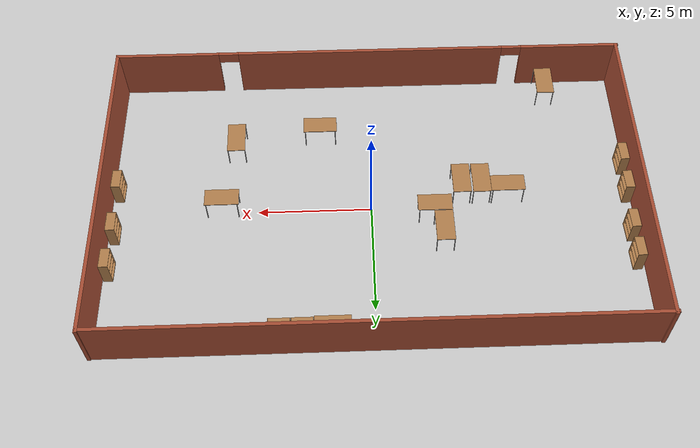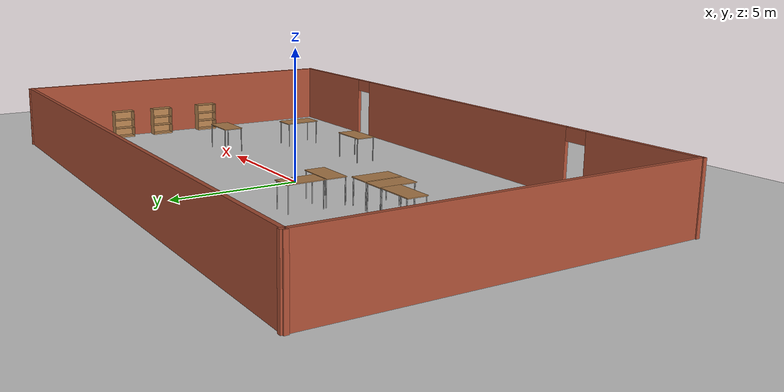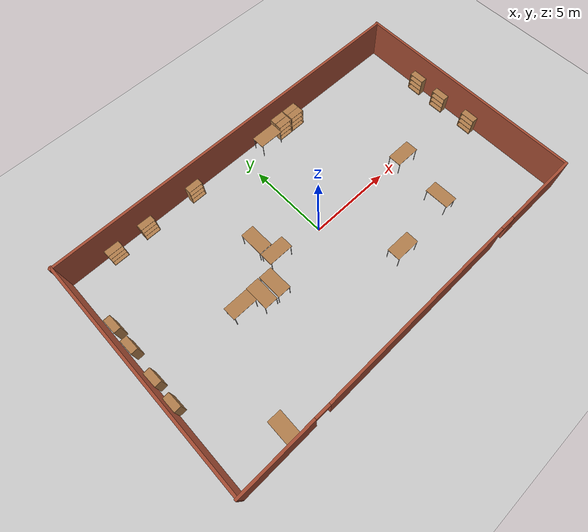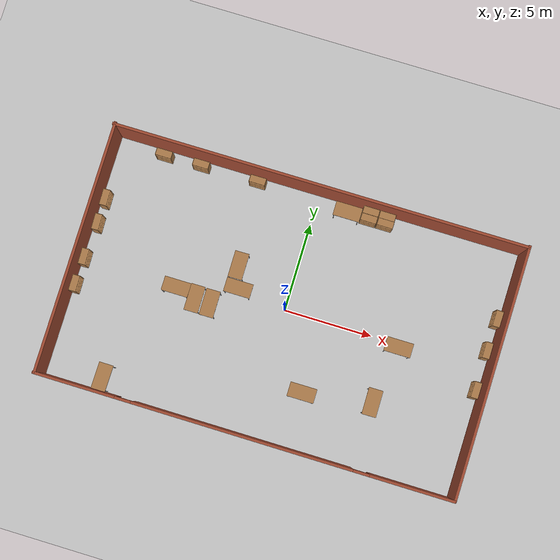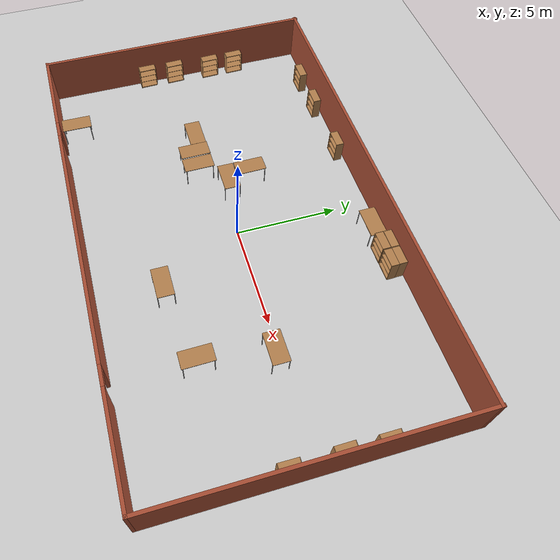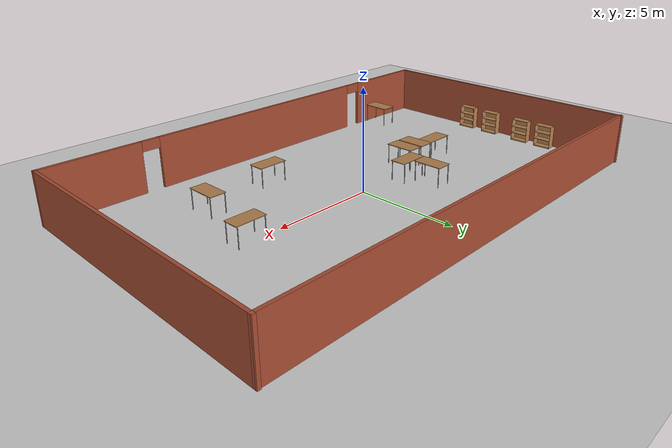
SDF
<sdf version="1.7">
 <world name="default">
  <light name="sun" type="directional">
   <pose>0 0 10 0 -0 0</pose>
   <diffuse>0.8 0.8 0.8 1</diffuse>
   <specular>0.2 0.2 0.2 1</specular>
   <attenuation>
    <range>1000</range>
    <constant>0.9</constant>
    <linear>0.01</linear>
    <quadratic>0.001</quadratic>
   </attenuation>
   <direction>-0.5 0.1 -0.9</direction>
   <spot><inner_angle>0</inner_angle><outer_angle>0</outer_angle><falloff>0</falloff></spot>
  </light>
  <model name="ground_plane">
   <static>1</static>
   <link name="link">
    <collision name="collision">
     <geometry><plane><normal>0 0 1</normal><size>100 100</size></plane></geometry>
     <surface><friction><ode><mu>100</mu><mu2>50</mu2></ode></friction></surface>
    </collision>
    <visual name="visual">
     <cast_shadows>0</cast_shadows>
     <geometry><plane><normal>0 0 1</normal><size>100 100</size></plane></geometry>
     <material>
      <script><uri>file://media/materials/scripts/gazebo.material</uri><name>Gazebo/Grey</name></script>
     </material>
    </visual>
   </link>
  </model>
  <gravity>0 0 -9.8</gravity>
  <magnetic_field>6e-06 2.3e-05 -4.2e-05</magnetic_field>
  <atmosphere type="adiabatic"/>
  <physics type="ode">
   <max_step_size>0.001</max_step_size>
   <real_time_factor>1</real_time_factor>
   <real_time_update_rate>1000</real_time_update_rate>
  </physics>
  <scene><ambient>0.4 0.4 0.4 1</ambient><background>0.7 0.7 0.7 1</background><shadows>1</shadows></scene>
  <audio><device>default</device></audio>
  <spherical_coordinates>
   <surface_model>EARTH_WGS84</surface_model>
   <latitude_deg>0</latitude_deg>
   <longitude_deg>0</longitude_deg>
   <elevation>0</elevation>
   <heading_deg>0</heading_deg>
  </spherical_coordinates>
  <model name="lab_experimental">
   <pose>-0.043326 -0.210443 0 0 -0 0</pose>
   <link name="Wall_0">
    <collision name="Wall_0_Collision">
     <geometry><box><size>23.5 0.15 2.5</size></box></geometry>
     <pose>0 0 1.25 0 -0 0</pose>
    </collision>
    <visual name="Wall_0_Visual">
     <pose>0 0 1.25 0 -0 0</pose>
     <geometry><box><size>23.5 0.15 2.5</size></box></geometry>
     <material>
      <script><uri>file://media/materials/scripts/gazebo.material</uri><name>Gazebo/Bricks</name></script>
      <ambient>1 1 1 1</ambient>
     </material>
     <meta><layer>0</layer></meta>
    </visual>
    <pose>-0.000322 7.01118 0 0 -0 0</pose>
   </link>
   <link name="Wall_1">
    <collision name="Wall_1_Collision">
     <geometry><box><size>14.2319 0.15 2.5</size></box></geometry>
     <pose>0 0 1.25 0 -0 0</pose>
    </collision>
    <visual name="Wall_1_Visual">
     <pose>0 0 1.25 0 -0 0</pose>
     <geometry><box><size>14.2319 0.15 2.5</size></box></geometry>
     <material>
      <script><uri>file://media/materials/scripts/gazebo.material</uri><name>Gazebo/Bricks</name></script>
      <ambient>1 1 1 1</ambient>
     </material>
     <meta><layer>0</layer></meta>
    </visual>
    <pose>11.614 0.010965 0 0 -0 -1.57942</pose>
   </link>
   <link name="Wall_2">
    <pose>-0.053739 -7.04993 0 0 -0 3.13985</pose>
    <visual name="Wall_2_Visual_0">
     <pose>-9.30831 0 1.25 0 -0 0</pose>
     <geometry><box><size>4.74763 0.15 2.5</size></box></geometry>
     <material>
      <script><uri>file://media/materials/scripts/gazebo.material</uri><name>Gazebo/Bricks</name></script>
      <ambient>1 1 1 1</ambient>
     </material>
     <meta><layer>0</layer></meta>
    </visual>
    <collision name="Wall_2_Collision_0">
     <geometry><box><size>4.74763 0.15 2.5</size></box></geometry>
     <pose>-9.30831 0 1.25 0 -0 0</pose>
    </collision>
    <visual name="Wall_2_Visual_1">
     <pose>0.091294 0 1.25 0 -0 0</pose>
     <geometry><box><size>12.2516 0.15 2.5</size></box></geometry>
     <material>
      <script><uri>file://media/materials/scripts/gazebo.material</uri><name>Gazebo/Bricks</name></script>
      <ambient>1 1 1 1</ambient>
     </material>
     <meta><layer>0</layer></meta>
    </visual>
    <collision name="Wall_2_Collision_1">
     <geometry><box><size>12.2516 0.15 2.5</size></box></geometry>
     <pose>0.091294 0 1.25 0 -0 0</pose>
    </collision>
    <visual name="Wall_2_Visual_2">
     <pose>9.3996 0 1.25 0 -0 0</pose>
     <geometry><box><size>4.56504 0.15 2.5</size></box></geometry>
     <material>
      <script><uri>file://media/materials/scripts/gazebo.material</uri><name>Gazebo/Bricks</name></script>
      <ambient>1 1 1 1</ambient>
     </material>
     <meta><layer>0</layer></meta>
    </visual>
    <collision name="Wall_2_Collision_2">
     <geometry><box><size>4.56504 0.15 2.5</size></box></geometry>
     <pose>9.3996 0 1.25 0 -0 0</pose>
    </collision>
    <visual name="Wall_2_Visual_3">
     <pose>-6.48449 0 2.25 0 -0 0</pose>
     <geometry><box><size>0.9 0.15 0.5</size></box></geometry>
     <material>
      <script><uri>file://media/materials/scripts/gazebo.material</uri><name>Gazebo/Bricks</name></script>
      <ambient>1 1 1 1</ambient>
     </material>
     <meta><layer>0</layer></meta>
    </visual>
    <collision name="Wall_2_Collision_3">
     <geometry><box><size>0.9 0.15 0.5</size></box></geometry>
     <pose>-6.48449 0 2.25 0 -0 0</pose>
    </collision>
    <visual name="Wall_2_Visual_4">
     <pose>6.66708 0 2.25 0 -0 0</pose>
     <geometry><box><size>0.9 0.15 0.5</size></box></geometry>
     <material>
      <script><uri>file://media/materials/scripts/gazebo.material</uri><name>Gazebo/Bricks</name></script>
      <ambient>1 1 1 1</ambient>
     </material>
     <meta><layer>0</layer></meta>
    </visual>
    <collision name="Wall_2_Collision_4">
     <geometry><box><size>0.9 0.15 0.5</size></box></geometry>
     <pose>6.66708 0 2.25 0 -0 0</pose>
    </collision>
   </link>
   <link name="Wall_3">
    <collision name="Wall_3_Collision">
     <geometry><box><size>14.25 0.15 2.5</size></box></geometry>
     <pose>0 0 1.25 0 -0 0</pose>
    </collision>
    <visual name="Wall_3_Visual">
     <pose>0 0 1.25 0 -0 0</pose>
     <geometry><box><size>14.25 0.15 2.5</size></box></geometry>
     <material>
      <script><uri>file://media/materials/scripts/gazebo.material</uri><name>Gazebo/Bricks</name></script>
      <ambient>1 1 1 1</ambient>
     </material>
     <meta><layer>0</layer></meta>
    </visual>
    <pose>-11.6203 0.020293 0 0 -0 1.5708</pose>
   </link>
   <static>1</static>
  </model>
  <model name="bookshelf">
   <static>1</static>
   <link name="link">
    <inertial><mass>1</mass></inertial>
    <collision name="back">
     <pose>0 0.005 0.6 0 -0 0</pose>
     <geometry><box><size>0.9 0.01 1.2</size></box></geometry>
    </collision>
    <visual name="visual1">
     <pose>0 0.005 0.6 0 -0 0</pose>
     <geometry><box><size>0.9 0.01 1.2</size></box></geometry>
     <material>
      <script><uri>file://media/materials/scripts/gazebo.material</uri><name>Gazebo/Wood</name></script>
     </material>
    </visual>
    <collision name="left_side">
     <pose>0.45 -0.195 0.6 0 -0 0</pose>
     <geometry><box><size>0.02 0.4 1.2</size></box></geometry>
    </collision>
    <visual name="visual2">
     <pose>0.45 -0.195 0.6 0 -0 0</pose>
     <geometry><box><size>0.02 0.4 1.2</size></box></geometry>
     <material>
      <script><uri>file://media/materials/scripts/gazebo.material</uri><name>Gazebo/Wood</name></script>
     </material>
    </visual>
    <collision name="right_side">
     <pose>-0.45 -0.195 0.6 0 -0 0</pose>
     <geometry><box><size>0.02 0.4 1.2</size></box></geometry>
    </collision>
    <visual name="visual3">
     <pose>-0.45 -0.195 0.6 0 -0 0</pose>
     <geometry><box><size>0.02 0.4 1.2</size></box></geometry>
     <material>
      <script><uri>file://media/materials/scripts/gazebo.material</uri><name>Gazebo/Wood</name></script>
     </material>
    </visual>
    <collision name="bottom">
     <pose>0 -0.195 0.03 0 -0 0</pose>
     <geometry><box><size>0.88 0.4 0.06</size></box></geometry>
    </collision>
    <visual name="visual4">
     <pose>0 -0.195 0.03 0 -0 0</pose>
     <geometry><box><size>0.88 0.4 0.06</size></box></geometry>
     <material>
      <script><uri>file://media/materials/scripts/gazebo.material</uri><name>Gazebo/Wood</name></script>
     </material>
    </visual>
    <collision name="top">
     <pose>0 -0.195 1.19 0 -0 0</pose>
     <geometry><box><size>0.88 0.4 0.02</size></box></geometry>
    </collision>
    <visual name="visual5">
     <pose>0 -0.195 1.19 0 -0 0</pose>
     <geometry><box><size>0.88 0.4 0.02</size></box></geometry>
     <material>
      <script><uri>file://media/materials/scripts/gazebo.material</uri><name>Gazebo/Wood</name></script>
     </material>
    </visual>
    <collision name="low_shelf">
     <pose>0 -0.195 0.43 0 -0 0</pose>
     <geometry><box><size>0.88 0.4 0.02</size></box></geometry>
    </collision>
    <visual name="visual6">
     <pose>0 -0.195 0.43 0 -0 0</pose>
     <geometry><box><size>0.88 0.4 0.02</size></box></geometry>
     <material>
      <script><uri>file://media/materials/scripts/gazebo.material</uri><name>Gazebo/Wood</name></script>
     </material>
    </visual>
    <collision name="high_shelf">
     <pose>0 -0.195 0.8 0 -0 0</pose>
     <geometry><box><size>0.88 0.4 0.02</size></box></geometry>
    </collision>
    <visual name="visual7">
     <pose>0 -0.195 0.8 0 -0 0</pose>
     <geometry><box><size>0.88 0.4 0.02</size></box></geometry>
     <material>
      <script><uri>file://media/materials/scripts/gazebo.material</uri><name>Gazebo/Wood</name></script>
     </material>
    </visual>
   </link>
   <pose>-11.4399 1.57923 0 0 -0 1.59792</pose>
  </model>
  <model name="bookshelf_0">
   <static>1</static>
   <link name="link">
    <inertial><mass>1</mass></inertial>
    <collision name="back">
     <pose>0 0.005 0.6 0 -0 0</pose>
     <geometry><box><size>0.9 0.01 1.2</size></box></geometry>
    </collision>
    <visual name="visual1">
     <pose>0 0.005 0.6 0 -0 0</pose>
     <geometry><box><size>0.9 0.01 1.2</size></box></geometry>
     <material>
      <script><uri>file://media/materials/scripts/gazebo.material</uri><name>Gazebo/Wood</name></script>
     </material>
    </visual>
    <collision name="left_side">
     <pose>0.45 -0.195 0.6 0 -0 0</pose>
     <geometry><box><size>0.02 0.4 1.2</size></box></geometry>
    </collision>
    <visual name="visual2">
     <pose>0.45 -0.195 0.6 0 -0 0</pose>
     <geometry><box><size>0.02 0.4 1.2</size></box></geometry>
     <material>
      <script><uri>file://media/materials/scripts/gazebo.material</uri><name>Gazebo/Wood</name></script>
     </material>
    </visual>
    <collision name="right_side">
     <pose>-0.45 -0.195 0.6 0 -0 0</pose>
     <geometry><box><size>0.02 0.4 1.2</size></box></geometry>
    </collision>
    <visual name="visual3">
     <pose>-0.45 -0.195 0.6 0 -0 0</pose>
     <geometry><box><size>0.02 0.4 1.2</size></box></geometry>
     <material>
      <script><uri>file://media/materials/scripts/gazebo.material</uri><name>Gazebo/Wood</name></script>
     </material>
    </visual>
    <collision name="bottom">
     <pose>0 -0.195 0.03 0 -0 0</pose>
     <geometry><box><size>0.88 0.4 0.06</size></box></geometry>
    </collision>
    <visual name="visual4">
     <pose>0 -0.195 0.03 0 -0 0</pose>
     <geometry><box><size>0.88 0.4 0.06</size></box></geometry>
     <material>
      <script><uri>file://media/materials/scripts/gazebo.material</uri><name>Gazebo/Wood</name></script>
     </material>
    </visual>
    <collision name="top">
     <pose>0 -0.195 1.19 0 -0 0</pose>
     <geometry><box><size>0.88 0.4 0.02</size></box></geometry>
    </collision>
    <visual name="visual5">
     <pose>0 -0.195 1.19 0 -0 0</pose>
     <geometry><box><size>0.88 0.4 0.02</size></box></geometry>
     <material>
      <script><uri>file://media/materials/scripts/gazebo.material</uri><name>Gazebo/Wood</name></script>
     </material>
    </visual>
    <collision name="low_shelf">
     <pose>0 -0.195 0.43 0 -0 0</pose>
     <geometry><box><size>0.88 0.4 0.02</size></box></geometry>
    </collision>
    <visual name="visual6">
     <pose>0 -0.195 0.43 0 -0 0</pose>
     <geometry><box><size>0.88 0.4 0.02</size></box></geometry>
     <material>
      <script><uri>file://media/materials/scripts/gazebo.material</uri><name>Gazebo/Wood</name></script>
     </material>
    </visual>
    <collision name="high_shelf">
     <pose>0 -0.195 0.8 0 -0 0</pose>
     <geometry><box><size>0.88 0.4 0.02</size></box></geometry>
    </collision>
    <visual name="visual7">
     <pose>0 -0.195 0.8 0 -0 0</pose>
     <geometry><box><size>0.88 0.4 0.02</size></box></geometry>
     <material>
      <script><uri>file://media/materials/scripts/gazebo.material</uri><name>Gazebo/Wood</name></script>
     </material>
    </visual>
   </link>
   <pose>-6.73791 6.53013 0 0 -0 0</pose>
  </model>
  <model name="bookshelf_1">
   <static>1</static>
   <link name="link">
    <inertial><mass>1</mass></inertial>
    <collision name="back">
     <pose>0 0.005 0.6 0 -0 0</pose>
     <geometry><box><size>0.9 0.01 1.2</size></box></geometry>
    </collision>
    <visual name="visual1">
     <pose>0 0.005 0.6 0 -0 0</pose>
     <geometry><box><size>0.9 0.01 1.2</size></box></geometry>
     <material>
      <script><uri>file://media/materials/scripts/gazebo.material</uri><name>Gazebo/Wood</name></script>
     </material>
    </visual>
    <collision name="left_side">
     <pose>0.45 -0.195 0.6 0 -0 0</pose>
     <geometry><box><size>0.02 0.4 1.2</size></box></geometry>
    </collision>
    <visual name="visual2">
     <pose>0.45 -0.195 0.6 0 -0 0</pose>
     <geometry><box><size>0.02 0.4 1.2</size></box></geometry>
     <material>
      <script><uri>file://media/materials/scripts/gazebo.material</uri><name>Gazebo/Wood</name></script>
     </material>
    </visual>
    <collision name="right_side">
     <pose>-0.45 -0.195 0.6 0 -0 0</pose>
     <geometry><box><size>0.02 0.4 1.2</size></box></geometry>
    </collision>
    <visual name="visual3">
     <pose>-0.45 -0.195 0.6 0 -0 0</pose>
     <geometry><box><size>0.02 0.4 1.2</size></box></geometry>
     <material>
      <script><uri>file://media/materials/scripts/gazebo.material</uri><name>Gazebo/Wood</name></script>
     </material>
    </visual>
    <collision name="bottom">
     <pose>0 -0.195 0.03 0 -0 0</pose>
     <geometry><box><size>0.88 0.4 0.06</size></box></geometry>
    </collision>
    <visual name="visual4">
     <pose>0 -0.195 0.03 0 -0 0</pose>
     <geometry><box><size>0.88 0.4 0.06</size></box></geometry>
     <material>
      <script><uri>file://media/materials/scripts/gazebo.material</uri><name>Gazebo/Wood</name></script>
     </material>
    </visual>
    <collision name="top">
     <pose>0 -0.195 1.19 0 -0 0</pose>
     <geometry><box><size>0.88 0.4 0.02</size></box></geometry>
    </collision>
    <visual name="visual5">
     <pose>0 -0.195 1.19 0 -0 0</pose>
     <geometry><box><size>0.88 0.4 0.02</size></box></geometry>
     <material>
      <script><uri>file://media/materials/scripts/gazebo.material</uri><name>Gazebo/Wood</name></script>
     </material>
    </visual>
    <collision name="low_shelf">
     <pose>0 -0.195 0.43 0 -0 0</pose>
     <geometry><box><size>0.88 0.4 0.02</size></box></geometry>
    </collision>
    <visual name="visual6">
     <pose>0 -0.195 0.43 0 -0 0</pose>
     <geometry><box><size>0.88 0.4 0.02</size></box></geometry>
     <material>
      <script><uri>file://media/materials/scripts/gazebo.material</uri><name>Gazebo/Wood</name></script>
     </material>
    </visual>
    <collision name="high_shelf">
     <pose>0 -0.195 0.8 0 -0 0</pose>
     <geometry><box><size>0.88 0.4 0.02</size></box></geometry>
    </collision>
    <visual name="visual7">
     <pose>0 -0.195 0.8 0 -0 0</pose>
     <geometry><box><size>0.88 0.4 0.02</size></box></geometry>
     <material>
      <script><uri>file://media/materials/scripts/gazebo.material</uri><name>Gazebo/Wood</name></script>
     </material>
    </visual>
   </link>
   <pose>-8.86607 6.49565 0 0 -0 0</pose>
  </model>
  <model name="bookshelf_2">
   <static>1</static>
   <link name="link">
    <inertial><mass>1</mass></inertial>
    <collision name="back">
     <pose>0 0.005 0.6 0 -0 0</pose>
     <geometry><box><size>0.9 0.01 1.2</size></box></geometry>
    </collision>
    <visual name="visual1">
     <pose>0 0.005 0.6 0 -0 0</pose>
     <geometry><box><size>0.9 0.01 1.2</size></box></geometry>
     <material>
      <script><uri>file://media/materials/scripts/gazebo.material</uri><name>Gazebo/Wood</name></script>
     </material>
    </visual>
    <collision name="left_side">
     <pose>0.45 -0.195 0.6 0 -0 0</pose>
     <geometry><box><size>0.02 0.4 1.2</size></box></geometry>
    </collision>
    <visual name="visual2">
     <pose>0.45 -0.195 0.6 0 -0 0</pose>
     <geometry><box><size>0.02 0.4 1.2</size></box></geometry>
     <material>
      <script><uri>file://media/materials/scripts/gazebo.material</uri><name>Gazebo/Wood</name></script>
     </material>
    </visual>
    <collision name="right_side">
     <pose>-0.45 -0.195 0.6 0 -0 0</pose>
     <geometry><box><size>0.02 0.4 1.2</size></box></geometry>
    </collision>
    <visual name="visual3">
     <pose>-0.45 -0.195 0.6 0 -0 0</pose>
     <geometry><box><size>0.02 0.4 1.2</size></box></geometry>
     <material>
      <script><uri>file://media/materials/scripts/gazebo.material</uri><name>Gazebo/Wood</name></script>
     </material>
    </visual>
    <collision name="bottom">
     <pose>0 -0.195 0.03 0 -0 0</pose>
     <geometry><box><size>0.88 0.4 0.06</size></box></geometry>
    </collision>
    <visual name="visual4">
     <pose>0 -0.195 0.03 0 -0 0</pose>
     <geometry><box><size>0.88 0.4 0.06</size></box></geometry>
     <material>
      <script><uri>file://media/materials/scripts/gazebo.material</uri><name>Gazebo/Wood</name></script>
     </material>
    </visual>
    <collision name="top">
     <pose>0 -0.195 1.19 0 -0 0</pose>
     <geometry><box><size>0.88 0.4 0.02</size></box></geometry>
    </collision>
    <visual name="visual5">
     <pose>0 -0.195 1.19 0 -0 0</pose>
     <geometry><box><size>0.88 0.4 0.02</size></box></geometry>
     <material>
      <script><uri>file://media/materials/scripts/gazebo.material</uri><name>Gazebo/Wood</name></script>
     </material>
    </visual>
    <collision name="low_shelf">
     <pose>0 -0.195 0.43 0 -0 0</pose>
     <geometry><box><size>0.88 0.4 0.02</size></box></geometry>
    </collision>
    <visual name="visual6">
     <pose>0 -0.195 0.43 0 -0 0</pose>
     <geometry><box><size>0.88 0.4 0.02</size></box></geometry>
     <material>
      <script><uri>file://media/materials/scripts/gazebo.material</uri><name>Gazebo/Wood</name></script>
     </material>
    </visual>
    <collision name="high_shelf">
     <pose>0 -0.195 0.8 0 -0 0</pose>
     <geometry><box><size>0.88 0.4 0.02</size></box></geometry>
    </collision>
    <visual name="visual7">
     <pose>0 -0.195 0.8 0 -0 0</pose>
     <geometry><box><size>0.88 0.4 0.02</size></box></geometry>
     <material>
      <script><uri>file://media/materials/scripts/gazebo.material</uri><name>Gazebo/Wood</name></script>
     </material>
    </visual>
   </link>
   <pose>-3.47886 6.55384 0 0 -0 0</pose>
  </model>
  <model name="bookshelf_clone">
   <static>1</static>
   <link name="link">
    <inertial><mass>1</mass></inertial>
    <collision name="back">
     <pose>0 0.005 0.6 0 -0 0</pose>
     <geometry><box><size>0.9 0.01 1.2</size></box></geometry>
    </collision>
    <visual name="visual1">
     <pose>0 0.005 0.6 0 -0 0</pose>
     <geometry><box><size>0.9 0.01 1.2</size></box></geometry>
     <material>
      <script><uri>file://media/materials/scripts/gazebo.material</uri><name>Gazebo/Wood</name></script>
     </material>
    </visual>
    <collision name="left_side">
     <pose>0.45 -0.195 0.6 0 -0 0</pose>
     <geometry><box><size>0.02 0.4 1.2</size></box></geometry>
    </collision>
    <visual name="visual2">
     <pose>0.45 -0.195 0.6 0 -0 0</pose>
     <geometry><box><size>0.02 0.4 1.2</size></box></geometry>
     <material>
      <script><uri>file://media/materials/scripts/gazebo.material</uri><name>Gazebo/Wood</name></script>
     </material>
    </visual>
    <collision name="right_side">
     <pose>-0.45 -0.195 0.6 0 -0 0</pose>
     <geometry><box><size>0.02 0.4 1.2</size></box></geometry>
    </collision>
    <visual name="visual3">
     <pose>-0.45 -0.195 0.6 0 -0 0</pose>
     <geometry><box><size>0.02 0.4 1.2</size></box></geometry>
     <material>
      <script><uri>file://media/materials/scripts/gazebo.material</uri><name>Gazebo/Wood</name></script>
     </material>
    </visual>
    <collision name="bottom">
     <pose>0 -0.195 0.03 0 -0 0</pose>
     <geometry><box><size>0.88 0.4 0.06</size></box></geometry>
    </collision>
    <visual name="visual4">
     <pose>0 -0.195 0.03 0 -0 0</pose>
     <geometry><box><size>0.88 0.4 0.06</size></box></geometry>
     <material>
      <script><uri>file://media/materials/scripts/gazebo.material</uri><name>Gazebo/Wood</name></script>
     </material>
    </visual>
    <collision name="top">
     <pose>0 -0.195 1.19 0 -0 0</pose>
     <geometry><box><size>0.88 0.4 0.02</size></box></geometry>
    </collision>
    <visual name="visual5">
     <pose>0 -0.195 1.19 0 -0 0</pose>
     <geometry><box><size>0.88 0.4 0.02</size></box></geometry>
     <material>
      <script><uri>file://media/materials/scripts/gazebo.material</uri><name>Gazebo/Wood</name></script>
     </material>
    </visual>
    <collision name="low_shelf">
     <pose>0 -0.195 0.43 0 -0 0</pose>
     <geometry><box><size>0.88 0.4 0.02</size></box></geometry>
    </collision>
    <visual name="visual6">
     <pose>0 -0.195 0.43 0 -0 0</pose>
     <geometry><box><size>0.88 0.4 0.02</size></box></geometry>
     <material>
      <script><uri>file://media/materials/scripts/gazebo.material</uri><name>Gazebo/Wood</name></script>
     </material>
    </visual>
    <collision name="high_shelf">
     <pose>0 -0.195 0.8 0 -0 0</pose>
     <geometry><box><size>0.88 0.4 0.02</size></box></geometry>
    </collision>
    <visual name="visual7">
     <pose>0 -0.195 0.8 0 -0 0</pose>
     <geometry><box><size>0.88 0.4 0.02</size></box></geometry>
     <material>
      <script><uri>file://media/materials/scripts/gazebo.material</uri><name>Gazebo/Wood</name></script>
     </material>
    </visual>
   </link>
   <pose>11.3923 -1.25194 0 0 0 -1.58716</pose>
  </model>
  <model name="bookshelf_clone_0">
   <static>1</static>
   <link name="link">
    <inertial><mass>1</mass></inertial>
    <collision name="back">
     <pose>0 0.005 0.6 0 -0 0</pose>
     <geometry><box><size>0.9 0.01 1.2</size></box></geometry>
    </collision>
    <visual name="visual1">
     <pose>0 0.005 0.6 0 -0 0</pose>
     <geometry><box><size>0.9 0.01 1.2</size></box></geometry>
     <material>
      <script><uri>file://media/materials/scripts/gazebo.material</uri><name>Gazebo/Wood</name></script>
     </material>
    </visual>
    <collision name="left_side">
     <pose>0.45 -0.195 0.6 0 -0 0</pose>
     <geometry><box><size>0.02 0.4 1.2</size></box></geometry>
    </collision>
    <visual name="visual2">
     <pose>0.45 -0.195 0.6 0 -0 0</pose>
     <geometry><box><size>0.02 0.4 1.2</size></box></geometry>
     <material>
      <script><uri>file://media/materials/scripts/gazebo.material</uri><name>Gazebo/Wood</name></script>
     </material>
    </visual>
    <collision name="right_side">
     <pose>-0.45 -0.195 0.6 0 -0 0</pose>
     <geometry><box><size>0.02 0.4 1.2</size></box></geometry>
    </collision>
    <visual name="visual3">
     <pose>-0.45 -0.195 0.6 0 -0 0</pose>
     <geometry><box><size>0.02 0.4 1.2</size></box></geometry>
     <material>
      <script><uri>file://media/materials/scripts/gazebo.material</uri><name>Gazebo/Wood</name></script>
     </material>
    </visual>
    <collision name="bottom">
     <pose>0 -0.195 0.03 0 -0 0</pose>
     <geometry><box><size>0.88 0.4 0.06</size></box></geometry>
    </collision>
    <visual name="visual4">
     <pose>0 -0.195 0.03 0 -0 0</pose>
     <geometry><box><size>0.88 0.4 0.06</size></box></geometry>
     <material>
      <script><uri>file://media/materials/scripts/gazebo.material</uri><name>Gazebo/Wood</name></script>
     </material>
    </visual>
    <collision name="top">
     <pose>0 -0.195 1.19 0 -0 0</pose>
     <geometry><box><size>0.88 0.4 0.02</size></box></geometry>
    </collision>
    <visual name="visual5">
     <pose>0 -0.195 1.19 0 -0 0</pose>
     <geometry><box><size>0.88 0.4 0.02</size></box></geometry>
     <material>
      <script><uri>file://media/materials/scripts/gazebo.material</uri><name>Gazebo/Wood</name></script>
     </material>
    </visual>
    <collision name="low_shelf">
     <pose>0 -0.195 0.43 0 -0 0</pose>
     <geometry><box><size>0.88 0.4 0.02</size></box></geometry>
    </collision>
    <visual name="visual6">
     <pose>0 -0.195 0.43 0 -0 0</pose>
     <geometry><box><size>0.88 0.4 0.02</size></box></geometry>
     <material>
      <script><uri>file://media/materials/scripts/gazebo.material</uri><name>Gazebo/Wood</name></script>
     </material>
    </visual>
    <collision name="high_shelf">
     <pose>0 -0.195 0.8 0 -0 0</pose>
     <geometry><box><size>0.88 0.4 0.02</size></box></geometry>
    </collision>
    <visual name="visual7">
     <pose>0 -0.195 0.8 0 -0 0</pose>
     <geometry><box><size>0.88 0.4 0.02</size></box></geometry>
     <material>
      <script><uri>file://media/materials/scripts/gazebo.material</uri><name>Gazebo/Wood</name></script>
     </material>
    </visual>
   </link>
   <pose>11.3961 0.993662 0 0 0 -1.57121</pose>
  </model>
  <model name="bookshelf_clone_1">
   <static>1</static>
   <link name="link">
    <inertial><mass>1</mass></inertial>
    <collision name="back">
     <pose>0 0.005 0.6 0 -0 0</pose>
     <geometry><box><size>0.9 0.01 1.2</size></box></geometry>
    </collision>
    <visual name="visual1">
     <pose>0 0.005 0.6 0 -0 0</pose>
     <geometry><box><size>0.9 0.01 1.2</size></box></geometry>
     <material>
      <script><uri>file://media/materials/scripts/gazebo.material</uri><name>Gazebo/Wood</name></script>
     </material>
    </visual>
    <collision name="left_side">
     <pose>0.45 -0.195 0.6 0 -0 0</pose>
     <geometry><box><size>0.02 0.4 1.2</size></box></geometry>
    </collision>
    <visual name="visual2">
     <pose>0.45 -0.195 0.6 0 -0 0</pose>
     <geometry><box><size>0.02 0.4 1.2</size></box></geometry>
     <material>
      <script><uri>file://media/materials/scripts/gazebo.material</uri><name>Gazebo/Wood</name></script>
     </material>
    </visual>
    <collision name="right_side">
     <pose>-0.45 -0.195 0.6 0 -0 0</pose>
     <geometry><box><size>0.02 0.4 1.2</size></box></geometry>
    </collision>
    <visual name="visual3">
     <pose>-0.45 -0.195 0.6 0 -0 0</pose>
     <geometry><box><size>0.02 0.4 1.2</size></box></geometry>
     <material>
      <script><uri>file://media/materials/scripts/gazebo.material</uri><name>Gazebo/Wood</name></script>
     </material>
    </visual>
    <collision name="bottom">
     <pose>0 -0.195 0.03 0 -0 0</pose>
     <geometry><box><size>0.88 0.4 0.06</size></box></geometry>
    </collision>
    <visual name="visual4">
     <pose>0 -0.195 0.03 0 -0 0</pose>
     <geometry><box><size>0.88 0.4 0.06</size></box></geometry>
     <material>
      <script><uri>file://media/materials/scripts/gazebo.material</uri><name>Gazebo/Wood</name></script>
     </material>
    </visual>
    <collision name="top">
     <pose>0 -0.195 1.19 0 -0 0</pose>
     <geometry><box><size>0.88 0.4 0.02</size></box></geometry>
    </collision>
    <visual name="visual5">
     <pose>0 -0.195 1.19 0 -0 0</pose>
     <geometry><box><size>0.88 0.4 0.02</size></box></geometry>
     <material>
      <script><uri>file://media/materials/scripts/gazebo.material</uri><name>Gazebo/Wood</name></script>
     </material>
    </visual>
    <collision name="low_shelf">
     <pose>0 -0.195 0.43 0 -0 0</pose>
     <geometry><box><size>0.88 0.4 0.02</size></box></geometry>
    </collision>
    <visual name="visual6">
     <pose>0 -0.195 0.43 0 -0 0</pose>
     <geometry><box><size>0.88 0.4 0.02</size></box></geometry>
     <material>
      <script><uri>file://media/materials/scripts/gazebo.material</uri><name>Gazebo/Wood</name></script>
     </material>
    </visual>
    <collision name="high_shelf">
     <pose>0 -0.195 0.8 0 -0 0</pose>
     <geometry><box><size>0.88 0.4 0.02</size></box></geometry>
    </collision>
    <visual name="visual7">
     <pose>0 -0.195 0.8 0 -0 0</pose>
     <geometry><box><size>0.88 0.4 0.02</size></box></geometry>
     <material>
      <script><uri>file://media/materials/scripts/gazebo.material</uri><name>Gazebo/Wood</name></script>
     </material>
    </visual>
   </link>
   <pose>11.4656 2.81029 0 0 0 -1.58232</pose>
  </model>
  <model name="table">
   <static>1</static>
   <link name="link">
    <collision name="surface">
     <pose>0 0 1 0 -0 0</pose>
     <geometry><box><size>1.5 0.8 0.03</size></box></geometry>
     <surface><friction><ode><mu>0.6</mu><mu2>0.6</mu2></ode></friction></surface>
    </collision>
    <visual name="visual1">
     <pose>0 0 1 0 -0 0</pose>
     <geometry><box><size>1.5 0.8 0.03</size></box></geometry>
     <material>
      <script><uri>file://media/materials/scripts/gazebo.material</uri><name>Gazebo/Wood</name></script>
     </material>
    </visual>
    <collision name="front_left_leg">
     <pose>0.68 0.38 0.5 0 -0 0</pose>
     <geometry><cylinder><radius>0.02</radius><length>1</length></cylinder></geometry>
    </collision>
    <visual name="front_left_leg">
     <pose>0.68 0.38 0.5 0 -0 0</pose>
     <geometry><cylinder><radius>0.02</radius><length>1</length></cylinder></geometry>
     <material>
      <script><uri>file://media/materials/scripts/gazebo.material</uri><name>Gazebo/Grey</name></script>
     </material>
    </visual>
    <collision name="front_right_leg">
     <pose>0.68 -0.38 0.5 0 -0 0</pose>
     <geometry><cylinder><radius>0.02</radius><length>1</length></cylinder></geometry>
    </collision>
    <visual name="front_right_leg">
     <pose>0.68 -0.38 0.5 0 -0 0</pose>
     <geometry><cylinder><radius>0.02</radius><length>1</length></cylinder></geometry>
     <material>
      <script><uri>file://media/materials/scripts/gazebo.material</uri><name>Gazebo/Grey</name></script>
     </material>
    </visual>
    <collision name="back_right_leg">
     <pose>-0.68 -0.38 0.5 0 -0 0</pose>
     <geometry><cylinder><radius>0.02</radius><length>1</length></cylinder></geometry>
    </collision>
    <visual name="back_right_leg">
     <pose>-0.68 -0.38 0.5 0 -0 0</pose>
     <geometry><cylinder><radius>0.02</radius><length>1</length></cylinder></geometry>
     <material>
      <script><uri>file://media/materials/scripts/gazebo.material</uri><name>Gazebo/Grey</name></script>
     </material>
    </visual>
    <collision name="back_left_leg">
     <pose>-0.68 0.38 0.5 0 -0 0</pose>
     <geometry><cylinder><radius>0.02</radius><length>1</length></cylinder></geometry>
    </collision>
    <visual name="back_left_leg">
     <pose>-0.68 0.38 0.5 0 -0 0</pose>
     <geometry><cylinder><radius>0.02</radius><length>1</length></cylinder></geometry>
     <material>
      <script><uri>file://media/materials/scripts/gazebo.material</uri><name>Gazebo/Grey</name></script>
     </material>
    </visual>
   </link>
   <pose>-6.03137 -0.564035 0 0 -0 0</pose>
  </model>
  <model name="table_clone">
   <static>1</static>
   <link name="link">
    <collision name="surface">
     <pose>0 0 1 0 -0 0</pose>
     <geometry><box><size>1.5 0.8 0.03</size></box></geometry>
     <surface><friction><ode><mu>0.6</mu><mu2>0.6</mu2></ode></friction></surface>
    </collision>
    <visual name="visual1">
     <pose>0 0 1 0 -0 0</pose>
     <geometry><box><size>1.5 0.8 0.03</size></box></geometry>
     <material>
      <script><uri>file://media/materials/scripts/gazebo.material</uri><name>Gazebo/Wood</name></script>
     </material>
    </visual>
    <collision name="front_left_leg">
     <pose>0.68 0.38 0.5 0 -0 0</pose>
     <geometry><cylinder><radius>0.02</radius><length>1</length></cylinder></geometry>
    </collision>
    <visual name="front_left_leg">
     <pose>0.68 0.38 0.5 0 -0 0</pose>
     <geometry><cylinder><radius>0.02</radius><length>1</length></cylinder></geometry>
     <material>
      <script><uri>file://media/materials/scripts/gazebo.material</uri><name>Gazebo/Grey</name></script>
     </material>
    </visual>
    <collision name="front_right_leg">
     <pose>0.68 -0.38 0.5 0 -0 0</pose>
     <geometry><cylinder><radius>0.02</radius><length>1</length></cylinder></geometry>
    </collision>
    <visual name="front_right_leg">
     <pose>0.68 -0.38 0.5 0 -0 0</pose>
     <geometry><cylinder><radius>0.02</radius><length>1</length></cylinder></geometry>
     <material>
      <script><uri>file://media/materials/scripts/gazebo.material</uri><name>Gazebo/Grey</name></script>
     </material>
    </visual>
    <collision name="back_right_leg">
     <pose>-0.68 -0.38 0.5 0 -0 0</pose>
     <geometry><cylinder><radius>0.02</radius><length>1</length></cylinder></geometry>
    </collision>
    <visual name="back_right_leg">
     <pose>-0.68 -0.38 0.5 0 -0 0</pose>
     <geometry><cylinder><radius>0.02</radius><length>1</length></cylinder></geometry>
     <material>
      <script><uri>file://media/materials/scripts/gazebo.material</uri><name>Gazebo/Grey</name></script>
     </material>
    </visual>
    <collision name="back_left_leg">
     <pose>-0.68 0.38 0.5 0 -0 0</pose>
     <geometry><cylinder><radius>0.02</radius><length>1</length></cylinder></geometry>
    </collision>
    <visual name="back_left_leg">
     <pose>-0.68 0.38 0.5 0 -0 0</pose>
     <geometry><cylinder><radius>0.02</radius><length>1</length></cylinder></geometry>
     <material>
      <script><uri>file://media/materials/scripts/gazebo.material</uri><name>Gazebo/Grey</name></script>
     </material>
    </visual>
   </link>
   <pose>-3.10998 1.54943 0 0 0 -1.56352</pose>
  </model>
  <model name="table_clone_0">
   <static>1</static>
   <link name="link">
    <collision name="surface">
     <pose>0 0 1 0 -0 0</pose>
     <geometry><box><size>1.5 0.8 0.03</size></box></geometry>
     <surface><friction><ode><mu>0.6</mu><mu2>0.6</mu2></ode></friction></surface>
    </collision>
    <visual name="visual1">
     <pose>0 0 1 0 -0 0</pose>
     <geometry><box><size>1.5 0.8 0.03</size></box></geometry>
     <material>
      <script><uri>file://media/materials/scripts/gazebo.material</uri><name>Gazebo/Wood</name></script>
     </material>
    </visual>
    <collision name="front_left_leg">
     <pose>0.68 0.38 0.5 0 -0 0</pose>
     <geometry><cylinder><radius>0.02</radius><length>1</length></cylinder></geometry>
    </collision>
    <visual name="front_left_leg">
     <pose>0.68 0.38 0.5 0 -0 0</pose>
     <geometry><cylinder><radius>0.02</radius><length>1</length></cylinder></geometry>
     <material>
      <script><uri>file://media/materials/scripts/gazebo.material</uri><name>Gazebo/Grey</name></script>
     </material>
    </visual>
    <collision name="front_right_leg">
     <pose>0.68 -0.38 0.5 0 -0 0</pose>
     <geometry><cylinder><radius>0.02</radius><length>1</length></cylinder></geometry>
    </collision>
    <visual name="front_right_leg">
     <pose>0.68 -0.38 0.5 0 -0 0</pose>
     <geometry><cylinder><radius>0.02</radius><length>1</length></cylinder></geometry>
     <material>
      <script><uri>file://media/materials/scripts/gazebo.material</uri><name>Gazebo/Grey</name></script>
     </material>
    </visual>
    <collision name="back_right_leg">
     <pose>-0.68 -0.38 0.5 0 -0 0</pose>
     <geometry><cylinder><radius>0.02</radius><length>1</length></cylinder></geometry>
    </collision>
    <visual name="back_right_leg">
     <pose>-0.68 -0.38 0.5 0 -0 0</pose>
     <geometry><cylinder><radius>0.02</radius><length>1</length></cylinder></geometry>
     <material>
      <script><uri>file://media/materials/scripts/gazebo.material</uri><name>Gazebo/Grey</name></script>
     </material>
    </visual>
    <collision name="back_left_leg">
     <pose>-0.68 0.38 0.5 0 -0 0</pose>
     <geometry><cylinder><radius>0.02</radius><length>1</length></cylinder></geometry>
    </collision>
    <visual name="back_left_leg">
     <pose>-0.68 0.38 0.5 0 -0 0</pose>
     <geometry><cylinder><radius>0.02</radius><length>1</length></cylinder></geometry>
     <material>
      <script><uri>file://media/materials/scripts/gazebo.material</uri><name>Gazebo/Grey</name></script>
     </material>
    </visual>
   </link>
   <pose>-2.75473 0.361404 0 0 -0 0</pose>
  </model>
  <model name="table_clone_1">
   <static>1</static>
   <link name="link">
    <collision name="surface">
     <pose>0 0 1 0 -0 0</pose>
     <geometry><box><size>1.5 0.8 0.03</size></box></geometry>
     <surface><friction><ode><mu>0.6</mu><mu2>0.6</mu2></ode></friction></surface>
    </collision>
    <visual name="visual1">
     <pose>0 0 1 0 -0 0</pose>
     <geometry><box><size>1.5 0.8 0.03</size></box></geometry>
     <material>
      <script><uri>file://media/materials/scripts/gazebo.material</uri><name>Gazebo/Wood</name></script>
     </material>
    </visual>
    <collision name="front_left_leg">
     <pose>0.68 0.38 0.5 0 -0 0</pose>
     <geometry><cylinder><radius>0.02</radius><length>1</length></cylinder></geometry>
    </collision>
    <visual name="front_left_leg">
     <pose>0.68 0.38 0.5 0 -0 0</pose>
     <geometry><cylinder><radius>0.02</radius><length>1</length></cylinder></geometry>
     <material>
      <script><uri>file://media/materials/scripts/gazebo.material</uri><name>Gazebo/Grey</name></script>
     </material>
    </visual>
    <collision name="front_right_leg">
     <pose>0.68 -0.38 0.5 0 -0 0</pose>
     <geometry><cylinder><radius>0.02</radius><length>1</length></cylinder></geometry>
    </collision>
    <visual name="front_right_leg">
     <pose>0.68 -0.38 0.5 0 -0 0</pose>
     <geometry><cylinder><radius>0.02</radius><length>1</length></cylinder></geometry>
     <material>
      <script><uri>file://media/materials/scripts/gazebo.material</uri><name>Gazebo/Grey</name></script>
     </material>
    </visual>
    <collision name="back_right_leg">
     <pose>-0.68 -0.38 0.5 0 -0 0</pose>
     <geometry><cylinder><radius>0.02</radius><length>1</length></cylinder></geometry>
    </collision>
    <visual name="back_right_leg">
     <pose>-0.68 -0.38 0.5 0 -0 0</pose>
     <geometry><cylinder><radius>0.02</radius><length>1</length></cylinder></geometry>
     <material>
      <script><uri>file://media/materials/scripts/gazebo.material</uri><name>Gazebo/Grey</name></script>
     </material>
    </visual>
    <collision name="back_left_leg">
     <pose>-0.68 0.38 0.5 0 -0 0</pose>
     <geometry><cylinder><radius>0.02</radius><length>1</length></cylinder></geometry>
    </collision>
    <visual name="back_left_leg">
     <pose>-0.68 0.38 0.5 0 -0 0</pose>
     <geometry><cylinder><radius>0.02</radius><length>1</length></cylinder></geometry>
     <material>
      <script><uri>file://media/materials/scripts/gazebo.material</uri><name>Gazebo/Grey</name></script>
     </material>
    </visual>
   </link>
   <pose>-8.39684 -6.4335 0 0 0 -1.582</pose>
  </model>
  <model name="bookshelf_clone_2">
   <static>1</static>
   <link name="link">
    <inertial><mass>1</mass></inertial>
    <collision name="back">
     <pose>0 0.005 0.6 0 -0 0</pose>
     <geometry><box><size>0.9 0.01 1.2</size></box></geometry>
    </collision>
    <visual name="visual1">
     <pose>0 0.005 0.6 0 -0 0</pose>
     <geometry><box><size>0.9 0.01 1.2</size></box></geometry>
     <material>
      <script><uri>file://media/materials/scripts/gazebo.material</uri><name>Gazebo/Wood</name></script>
     </material>
    </visual>
    <collision name="left_side">
     <pose>0.45 -0.195 0.6 0 -0 0</pose>
     <geometry><box><size>0.02 0.4 1.2</size></box></geometry>
    </collision>
    <visual name="visual2">
     <pose>0.45 -0.195 0.6 0 -0 0</pose>
     <geometry><box><size>0.02 0.4 1.2</size></box></geometry>
     <material>
      <script><uri>file://media/materials/scripts/gazebo.material</uri><name>Gazebo/Wood</name></script>
     </material>
    </visual>
    <collision name="right_side">
     <pose>-0.45 -0.195 0.6 0 -0 0</pose>
     <geometry><box><size>0.02 0.4 1.2</size></box></geometry>
    </collision>
    <visual name="visual3">
     <pose>-0.45 -0.195 0.6 0 -0 0</pose>
     <geometry><box><size>0.02 0.4 1.2</size></box></geometry>
     <material>
      <script><uri>file://media/materials/scripts/gazebo.material</uri><name>Gazebo/Wood</name></script>
     </material>
    </visual>
    <collision name="bottom">
     <pose>0 -0.195 0.03 0 -0 0</pose>
     <geometry><box><size>0.88 0.4 0.06</size></box></geometry>
    </collision>
    <visual name="visual4">
     <pose>0 -0.195 0.03 0 -0 0</pose>
     <geometry><box><size>0.88 0.4 0.06</size></box></geometry>
     <material>
      <script><uri>file://media/materials/scripts/gazebo.material</uri><name>Gazebo/Wood</name></script>
     </material>
    </visual>
    <collision name="top">
     <pose>0 -0.195 1.19 0 -0 0</pose>
     <geometry><box><size>0.88 0.4 0.02</size></box></geometry>
    </collision>
    <visual name="visual5">
     <pose>0 -0.195 1.19 0 -0 0</pose>
     <geometry><box><size>0.88 0.4 0.02</size></box></geometry>
     <material>
      <script><uri>file://media/materials/scripts/gazebo.material</uri><name>Gazebo/Wood</name></script>
     </material>
    </visual>
    <collision name="low_shelf">
     <pose>0 -0.195 0.43 0 -0 0</pose>
     <geometry><box><size>0.88 0.4 0.02</size></box></geometry>
    </collision>
    <visual name="visual6">
     <pose>0 -0.195 0.43 0 -0 0</pose>
     <geometry><box><size>0.88 0.4 0.02</size></box></geometry>
     <material>
      <script><uri>file://media/materials/scripts/gazebo.material</uri><name>Gazebo/Wood</name></script>
     </material>
    </visual>
    <collision name="high_shelf">
     <pose>0 -0.195 0.8 0 -0 0</pose>
     <geometry><box><size>0.88 0.4 0.02</size></box></geometry>
    </collision>
    <visual name="visual7">
     <pose>0 -0.195 0.8 0 -0 0</pose>
     <geometry><box><size>0.88 0.4 0.02</size></box></geometry>
     <material>
      <script><uri>file://media/materials/scripts/gazebo.material</uri><name>Gazebo/Wood</name></script>
     </material>
    </visual>
   </link>
   <pose>-11.4357 3 0 0 -0 1.59792</pose>
  </model>
  <model name="bookshelf_clone_3">
   <static>1</static>
   <link name="link">
    <inertial><mass>1</mass></inertial>
    <collision name="back">
     <pose>0 0.005 0.6 0 -0 0</pose>
     <geometry><box><size>0.9 0.01 1.2</size></box></geometry>
    </collision>
    <visual name="visual1">
     <pose>0 0.005 0.6 0 -0 0</pose>
     <geometry><box><size>0.9 0.01 1.2</size></box></geometry>
     <material>
      <script><uri>file://media/materials/scripts/gazebo.material</uri><name>Gazebo/Wood</name></script>
     </material>
    </visual>
    <collision name="left_side">
     <pose>0.45 -0.195 0.6 0 -0 0</pose>
     <geometry><box><size>0.02 0.4 1.2</size></box></geometry>
    </collision>
    <visual name="visual2">
     <pose>0.45 -0.195 0.6 0 -0 0</pose>
     <geometry><box><size>0.02 0.4 1.2</size></box></geometry>
     <material>
      <script><uri>file://media/materials/scripts/gazebo.material</uri><name>Gazebo/Wood</name></script>
     </material>
    </visual>
    <collision name="right_side">
     <pose>-0.45 -0.195 0.6 0 -0 0</pose>
     <geometry><box><size>0.02 0.4 1.2</size></box></geometry>
    </collision>
    <visual name="visual3">
     <pose>-0.45 -0.195 0.6 0 -0 0</pose>
     <geometry><box><size>0.02 0.4 1.2</size></box></geometry>
     <material>
      <script><uri>file://media/materials/scripts/gazebo.material</uri><name>Gazebo/Wood</name></script>
     </material>
    </visual>
    <collision name="bottom">
     <pose>0 -0.195 0.03 0 -0 0</pose>
     <geometry><box><size>0.88 0.4 0.06</size></box></geometry>
    </collision>
    <visual name="visual4">
     <pose>0 -0.195 0.03 0 -0 0</pose>
     <geometry><box><size>0.88 0.4 0.06</size></box></geometry>
     <material>
      <script><uri>file://media/materials/scripts/gazebo.material</uri><name>Gazebo/Wood</name></script>
     </material>
    </visual>
    <collision name="top">
     <pose>0 -0.195 1.19 0 -0 0</pose>
     <geometry><box><size>0.88 0.4 0.02</size></box></geometry>
    </collision>
    <visual name="visual5">
     <pose>0 -0.195 1.19 0 -0 0</pose>
     <geometry><box><size>0.88 0.4 0.02</size></box></geometry>
     <material>
      <script><uri>file://media/materials/scripts/gazebo.material</uri><name>Gazebo/Wood</name></script>
     </material>
    </visual>
    <collision name="low_shelf">
     <pose>0 -0.195 0.43 0 -0 0</pose>
     <geometry><box><size>0.88 0.4 0.02</size></box></geometry>
    </collision>
    <visual name="visual6">
     <pose>0 -0.195 0.43 0 -0 0</pose>
     <geometry><box><size>0.88 0.4 0.02</size></box></geometry>
     <material>
      <script><uri>file://media/materials/scripts/gazebo.material</uri><name>Gazebo/Wood</name></script>
     </material>
    </visual>
    <collision name="high_shelf">
     <pose>0 -0.195 0.8 0 -0 0</pose>
     <geometry><box><size>0.88 0.4 0.02</size></box></geometry>
    </collision>
    <visual name="visual7">
     <pose>0 -0.195 0.8 0 -0 0</pose>
     <geometry><box><size>0.88 0.4 0.02</size></box></geometry>
     <material>
      <script><uri>file://media/materials/scripts/gazebo.material</uri><name>Gazebo/Wood</name></script>
     </material>
    </visual>
   </link>
   <pose>-11.5445 -0.4554 0 0 -0 1.59792</pose>
  </model>
  <model name="bookshelf_clone_4">
   <static>1</static>
   <link name="link">
    <inertial><mass>1</mass></inertial>
    <collision name="back">
     <pose>0 0.005 0.6 0 -0 0</pose>
     <geometry><box><size>0.9 0.01 1.2</size></box></geometry>
    </collision>
    <visual name="visual1">
     <pose>0 0.005 0.6 0 -0 0</pose>
     <geometry><box><size>0.9 0.01 1.2</size></box></geometry>
     <material>
      <script><uri>file://media/materials/scripts/gazebo.material</uri><name>Gazebo/Wood</name></script>
     </material>
    </visual>
    <collision name="left_side">
     <pose>0.45 -0.195 0.6 0 -0 0</pose>
     <geometry><box><size>0.02 0.4 1.2</size></box></geometry>
    </collision>
    <visual name="visual2">
     <pose>0.45 -0.195 0.6 0 -0 0</pose>
     <geometry><box><size>0.02 0.4 1.2</size></box></geometry>
     <material>
      <script><uri>file://media/materials/scripts/gazebo.material</uri><name>Gazebo/Wood</name></script>
     </material>
    </visual>
    <collision name="right_side">
     <pose>-0.45 -0.195 0.6 0 -0 0</pose>
     <geometry><box><size>0.02 0.4 1.2</size></box></geometry>
    </collision>
    <visual name="visual3">
     <pose>-0.45 -0.195 0.6 0 -0 0</pose>
     <geometry><box><size>0.02 0.4 1.2</size></box></geometry>
     <material>
      <script><uri>file://media/materials/scripts/gazebo.material</uri><name>Gazebo/Wood</name></script>
     </material>
    </visual>
    <collision name="bottom">
     <pose>0 -0.195 0.03 0 -0 0</pose>
     <geometry><box><size>0.88 0.4 0.06</size></box></geometry>
    </collision>
    <visual name="visual4">
     <pose>0 -0.195 0.03 0 -0 0</pose>
     <geometry><box><size>0.88 0.4 0.06</size></box></geometry>
     <material>
      <script><uri>file://media/materials/scripts/gazebo.material</uri><name>Gazebo/Wood</name></script>
     </material>
    </visual>
    <collision name="top">
     <pose>0 -0.195 1.19 0 -0 0</pose>
     <geometry><box><size>0.88 0.4 0.02</size></box></geometry>
    </collision>
    <visual name="visual5">
     <pose>0 -0.195 1.19 0 -0 0</pose>
     <geometry><box><size>0.88 0.4 0.02</size></box></geometry>
     <material>
      <script><uri>file://media/materials/scripts/gazebo.material</uri><name>Gazebo/Wood</name></script>
     </material>
    </visual>
    <collision name="low_shelf">
     <pose>0 -0.195 0.43 0 -0 0</pose>
     <geometry><box><size>0.88 0.4 0.02</size></box></geometry>
    </collision>
    <visual name="visual6">
     <pose>0 -0.195 0.43 0 -0 0</pose>
     <geometry><box><size>0.88 0.4 0.02</size></box></geometry>
     <material>
      <script><uri>file://media/materials/scripts/gazebo.material</uri><name>Gazebo/Wood</name></script>
     </material>
    </visual>
    <collision name="high_shelf">
     <pose>0 -0.195 0.8 0 -0 0</pose>
     <geometry><box><size>0.88 0.4 0.02</size></box></geometry>
    </collision>
    <visual name="visual7">
     <pose>0 -0.195 0.8 0 -0 0</pose>
     <geometry><box><size>0.88 0.4 0.02</size></box></geometry>
     <material>
      <script><uri>file://media/materials/scripts/gazebo.material</uri><name>Gazebo/Wood</name></script>
     </material>
    </visual>
   </link>
   <pose>-11.5844 -2 0 0 -0 1.59792</pose>
  </model>
  <model name="table_clone_clone">
   <static>1</static>
   <link name="link">
    <collision name="surface">
     <pose>0 0 1 0 -0 0</pose>
     <geometry><box><size>1.5 0.8 0.03</size></box></geometry>
     <surface><friction><ode><mu>0.6</mu><mu2>0.6</mu2></ode></friction></surface>
    </collision>
    <visual name="visual1">
     <pose>0 0 1 0 -0 0</pose>
     <geometry><box><size>1.5 0.8 0.03</size></box></geometry>
     <material>
      <script><uri>file://media/materials/scripts/gazebo.material</uri><name>Gazebo/Wood</name></script>
     </material>
    </visual>
    <collision name="front_left_leg">
     <pose>0.68 0.38 0.5 0 -0 0</pose>
     <geometry><cylinder><radius>0.02</radius><length>1</length></cylinder></geometry>
    </collision>
    <visual name="front_left_leg">
     <pose>0.68 0.38 0.5 0 -0 0</pose>
     <geometry><cylinder><radius>0.02</radius><length>1</length></cylinder></geometry>
     <material>
      <script><uri>file://media/materials/scripts/gazebo.material</uri><name>Gazebo/Grey</name></script>
     </material>
    </visual>
    <collision name="front_right_leg">
     <pose>0.68 -0.38 0.5 0 -0 0</pose>
     <geometry><cylinder><radius>0.02</radius><length>1</length></cylinder></geometry>
    </collision>
    <visual name="front_right_leg">
     <pose>0.68 -0.38 0.5 0 -0 0</pose>
     <geometry><cylinder><radius>0.02</radius><length>1</length></cylinder></geometry>
     <material>
      <script><uri>file://media/materials/scripts/gazebo.material</uri><name>Gazebo/Grey</name></script>
     </material>
    </visual>
    <collision name="back_right_leg">
     <pose>-0.68 -0.38 0.5 0 -0 0</pose>
     <geometry><cylinder><radius>0.02</radius><length>1</length></cylinder></geometry>
    </collision>
    <visual name="back_right_leg">
     <pose>-0.68 -0.38 0.5 0 -0 0</pose>
     <geometry><cylinder><radius>0.02</radius><length>1</length></cylinder></geometry>
     <material>
      <script><uri>file://media/materials/scripts/gazebo.material</uri><name>Gazebo/Grey</name></script>
     </material>
    </visual>
    <collision name="back_left_leg">
     <pose>-0.68 0.38 0.5 0 -0 0</pose>
     <geometry><cylinder><radius>0.02</radius><length>1</length></cylinder></geometry>
    </collision>
    <visual name="back_left_leg">
     <pose>-0.68 0.38 0.5 0 -0 0</pose>
     <geometry><cylinder><radius>0.02</radius><length>1</length></cylinder></geometry>
     <material>
      <script><uri>file://media/materials/scripts/gazebo.material</uri><name>Gazebo/Grey</name></script>
     </material>
    </visual>
   </link>
   <pose>-4.003 -0.896875 0 0 0 -1.56352</pose>
  </model>
  <model name="table_clone_clone_0">
   <static>1</static>
   <link name="link">
    <collision name="surface">
     <pose>0 0 1 0 -0 0</pose>
     <geometry><box><size>1.5 0.8 0.03</size></box></geometry>
     <surface><friction><ode><mu>0.6</mu><mu2>0.6</mu2></ode></friction></surface>
    </collision>
    <visual name="visual1">
     <pose>0 0 1 0 -0 0</pose>
     <geometry><box><size>1.5 0.8 0.03</size></box></geometry>
     <material>
      <script><uri>file://media/materials/scripts/gazebo.material</uri><name>Gazebo/Wood</name></script>
     </material>
    </visual>
    <collision name="front_left_leg">
     <pose>0.68 0.38 0.5 0 -0 0</pose>
     <geometry><cylinder><radius>0.02</radius><length>1</length></cylinder></geometry>
    </collision>
    <visual name="front_left_leg">
     <pose>0.68 0.38 0.5 0 -0 0</pose>
     <geometry><cylinder><radius>0.02</radius><length>1</length></cylinder></geometry>
     <material>
      <script><uri>file://media/materials/scripts/gazebo.material</uri><name>Gazebo/Grey</name></script>
     </material>
    </visual>
    <collision name="front_right_leg">
     <pose>0.68 -0.38 0.5 0 -0 0</pose>
     <geometry><cylinder><radius>0.02</radius><length>1</length></cylinder></geometry>
    </collision>
    <visual name="front_right_leg">
     <pose>0.68 -0.38 0.5 0 -0 0</pose>
     <geometry><cylinder><radius>0.02</radius><length>1</length></cylinder></geometry>
     <material>
      <script><uri>file://media/materials/scripts/gazebo.material</uri><name>Gazebo/Grey</name></script>
     </material>
    </visual>
    <collision name="back_right_leg">
     <pose>-0.68 -0.38 0.5 0 -0 0</pose>
     <geometry><cylinder><radius>0.02</radius><length>1</length></cylinder></geometry>
    </collision>
    <visual name="back_right_leg">
     <pose>-0.68 -0.38 0.5 0 -0 0</pose>
     <geometry><cylinder><radius>0.02</radius><length>1</length></cylinder></geometry>
     <material>
      <script><uri>file://media/materials/scripts/gazebo.material</uri><name>Gazebo/Grey</name></script>
     </material>
    </visual>
    <collision name="back_left_leg">
     <pose>-0.68 0.38 0.5 0 -0 0</pose>
     <geometry><cylinder><radius>0.02</radius><length>1</length></cylinder></geometry>
    </collision>
    <visual name="back_left_leg">
     <pose>-0.68 0.38 0.5 0 -0 0</pose>
     <geometry><cylinder><radius>0.02</radius><length>1</length></cylinder></geometry>
     <material>
      <script><uri>file://media/materials/scripts/gazebo.material</uri><name>Gazebo/Grey</name></script>
     </material>
    </visual>
   </link>
   <pose>-4.8771 -0.883132 0 0 0 -1.56352</pose>
  </model>
  <model name="table_clone_clone_1">
   <static>1</static>
   <link name="link">
    <collision name="surface">
     <pose>0 0 1 0 -0 0</pose>
     <geometry><box><size>1.5 0.8 0.03</size></box></geometry>
     <surface><friction><ode><mu>0.6</mu><mu2>0.6</mu2></ode></friction></surface>
    </collision>
    <visual name="visual1">
     <pose>0 0 1 0 -0 0</pose>
     <geometry><box><size>1.5 0.8 0.03</size></box></geometry>
     <material>
      <script><uri>file://media/materials/scripts/gazebo.material</uri><name>Gazebo/Wood</name></script>
     </material>
    </visual>
    <collision name="front_left_leg">
     <pose>0.68 0.38 0.5 0 -0 0</pose>
     <geometry><cylinder><radius>0.02</radius><length>1</length></cylinder></geometry>
    </collision>
    <visual name="front_left_leg">
     <pose>0.68 0.38 0.5 0 -0 0</pose>
     <geometry><cylinder><radius>0.02</radius><length>1</length></cylinder></geometry>
     <material>
      <script><uri>file://media/materials/scripts/gazebo.material</uri><name>Gazebo/Grey</name></script>
     </material>
    </visual>
    <collision name="front_right_leg">
     <pose>0.68 -0.38 0.5 0 -0 0</pose>
     <geometry><cylinder><radius>0.02</radius><length>1</length></cylinder></geometry>
    </collision>
    <visual name="front_right_leg">
     <pose>0.68 -0.38 0.5 0 -0 0</pose>
     <geometry><cylinder><radius>0.02</radius><length>1</length></cylinder></geometry>
     <material>
      <script><uri>file://media/materials/scripts/gazebo.material</uri><name>Gazebo/Grey</name></script>
     </material>
    </visual>
    <collision name="back_right_leg">
     <pose>-0.68 -0.38 0.5 0 -0 0</pose>
     <geometry><cylinder><radius>0.02</radius><length>1</length></cylinder></geometry>
    </collision>
    <visual name="back_right_leg">
     <pose>-0.68 -0.38 0.5 0 -0 0</pose>
     <geometry><cylinder><radius>0.02</radius><length>1</length></cylinder></geometry>
     <material>
      <script><uri>file://media/materials/scripts/gazebo.material</uri><name>Gazebo/Grey</name></script>
     </material>
    </visual>
    <collision name="back_left_leg">
     <pose>-0.68 0.38 0.5 0 -0 0</pose>
     <geometry><cylinder><radius>0.02</radius><length>1</length></cylinder></geometry>
    </collision>
    <visual name="back_left_leg">
     <pose>-0.68 0.38 0.5 0 -0 0</pose>
     <geometry><cylinder><radius>0.02</radius><length>1</length></cylinder></geometry>
     <material>
      <script><uri>file://media/materials/scripts/gazebo.material</uri><name>Gazebo/Grey</name></script>
     </material>
    </visual>
   </link>
   <pose>6.02324 -3.50357 0 0 0 -1.56352</pose>
  </model>
  <model name="bookshelf_2_clone">
   <static>1</static>
   <link name="link">
    <inertial><mass>1</mass></inertial>
    <collision name="back">
     <pose>0 0.005 0.6 0 -0 0</pose>
     <geometry><box><size>0.9 0.01 1.2</size></box></geometry>
    </collision>
    <visual name="visual1">
     <pose>0 0.005 0.6 0 -0 0</pose>
     <geometry><box><size>0.9 0.01 1.2</size></box></geometry>
     <material>
      <script><uri>file://media/materials/scripts/gazebo.material</uri><name>Gazebo/Wood</name></script>
     </material>
    </visual>
    <collision name="left_side">
     <pose>0.45 -0.195 0.6 0 -0 0</pose>
     <geometry><box><size>0.02 0.4 1.2</size></box></geometry>
    </collision>
    <visual name="visual2">
     <pose>0.45 -0.195 0.6 0 -0 0</pose>
     <geometry><box><size>0.02 0.4 1.2</size></box></geometry>
     <material>
      <script><uri>file://media/materials/scripts/gazebo.material</uri><name>Gazebo/Wood</name></script>
     </material>
    </visual>
    <collision name="right_side">
     <pose>-0.45 -0.195 0.6 0 -0 0</pose>
     <geometry><box><size>0.02 0.4 1.2</size></box></geometry>
    </collision>
    <visual name="visual3">
     <pose>-0.45 -0.195 0.6 0 -0 0</pose>
     <geometry><box><size>0.02 0.4 1.2</size></box></geometry>
     <material>
      <script><uri>file://media/materials/scripts/gazebo.material</uri><name>Gazebo/Wood</name></script>
     </material>
    </visual>
    <collision name="bottom">
     <pose>0 -0.195 0.03 0 -0 0</pose>
     <geometry><box><size>0.88 0.4 0.06</size></box></geometry>
    </collision>
    <visual name="visual4">
     <pose>0 -0.195 0.03 0 -0 0</pose>
     <geometry><box><size>0.88 0.4 0.06</size></box></geometry>
     <material>
      <script><uri>file://media/materials/scripts/gazebo.material</uri><name>Gazebo/Wood</name></script>
     </material>
    </visual>
    <collision name="top">
     <pose>0 -0.195 1.19 0 -0 0</pose>
     <geometry><box><size>0.88 0.4 0.02</size></box></geometry>
    </collision>
    <visual name="visual5">
     <pose>0 -0.195 1.19 0 -0 0</pose>
     <geometry><box><size>0.88 0.4 0.02</size></box></geometry>
     <material>
      <script><uri>file://media/materials/scripts/gazebo.material</uri><name>Gazebo/Wood</name></script>
     </material>
    </visual>
    <collision name="low_shelf">
     <pose>0 -0.195 0.43 0 -0 0</pose>
     <geometry><box><size>0.88 0.4 0.02</size></box></geometry>
    </collision>
    <visual name="visual6">
     <pose>0 -0.195 0.43 0 -0 0</pose>
     <geometry><box><size>0.88 0.4 0.02</size></box></geometry>
     <material>
      <script><uri>file://media/materials/scripts/gazebo.material</uri><name>Gazebo/Wood</name></script>
     </material>
    </visual>
    <collision name="high_shelf">
     <pose>0 -0.195 0.8 0 -0 0</pose>
     <geometry><box><size>0.88 0.4 0.02</size></box></geometry>
    </collision>
    <visual name="visual7">
     <pose>0 -0.195 0.8 0 -0 0</pose>
     <geometry><box><size>0.88 0.4 0.02</size></box></geometry>
     <material>
      <script><uri>file://media/materials/scripts/gazebo.material</uri><name>Gazebo/Wood</name></script>
     </material>
    </visual>
   </link>
   <pose>2.99493 6.69161 0 0 -0 0</pose>
  </model>
  <model name="bookshelf_2_clone_0">
   <static>1</static>
   <link name="link">
    <inertial><mass>1</mass></inertial>
    <collision name="back">
     <pose>0 0.005 0.6 0 -0 0</pose>
     <geometry><box><size>0.9 0.01 1.2</size></box></geometry>
    </collision>
    <visual name="visual1">
     <pose>0 0.005 0.6 0 -0 0</pose>
     <geometry><box><size>0.9 0.01 1.2</size></box></geometry>
     <material>
      <script><uri>file://media/materials/scripts/gazebo.material</uri><name>Gazebo/Wood</name></script>
     </material>
    </visual>
    <collision name="left_side">
     <pose>0.45 -0.195 0.6 0 -0 0</pose>
     <geometry><box><size>0.02 0.4 1.2</size></box></geometry>
    </collision>
    <visual name="visual2">
     <pose>0.45 -0.195 0.6 0 -0 0</pose>
     <geometry><box><size>0.02 0.4 1.2</size></box></geometry>
     <material>
      <script><uri>file://media/materials/scripts/gazebo.material</uri><name>Gazebo/Wood</name></script>
     </material>
    </visual>
    <collision name="right_side">
     <pose>-0.45 -0.195 0.6 0 -0 0</pose>
     <geometry><box><size>0.02 0.4 1.2</size></box></geometry>
    </collision>
    <visual name="visual3">
     <pose>-0.45 -0.195 0.6 0 -0 0</pose>
     <geometry><box><size>0.02 0.4 1.2</size></box></geometry>
     <material>
      <script><uri>file://media/materials/scripts/gazebo.material</uri><name>Gazebo/Wood</name></script>
     </material>
    </visual>
    <collision name="bottom">
     <pose>0 -0.195 0.03 0 -0 0</pose>
     <geometry><box><size>0.88 0.4 0.06</size></box></geometry>
    </collision>
    <visual name="visual4">
     <pose>0 -0.195 0.03 0 -0 0</pose>
     <geometry><box><size>0.88 0.4 0.06</size></box></geometry>
     <material>
      <script><uri>file://media/materials/scripts/gazebo.material</uri><name>Gazebo/Wood</name></script>
     </material>
    </visual>
    <collision name="top">
     <pose>0 -0.195 1.19 0 -0 0</pose>
     <geometry><box><size>0.88 0.4 0.02</size></box></geometry>
    </collision>
    <visual name="visual5">
     <pose>0 -0.195 1.19 0 -0 0</pose>
     <geometry><box><size>0.88 0.4 0.02</size></box></geometry>
     <material>
      <script><uri>file://media/materials/scripts/gazebo.material</uri><name>Gazebo/Wood</name></script>
     </material>
    </visual>
    <collision name="low_shelf">
     <pose>0 -0.195 0.43 0 -0 0</pose>
     <geometry><box><size>0.88 0.4 0.02</size></box></geometry>
    </collision>
    <visual name="visual6">
     <pose>0 -0.195 0.43 0 -0 0</pose>
     <geometry><box><size>0.88 0.4 0.02</size></box></geometry>
     <material>
      <script><uri>file://media/materials/scripts/gazebo.material</uri><name>Gazebo/Wood</name></script>
     </material>
    </visual>
    <collision name="high_shelf">
     <pose>0 -0.195 0.8 0 -0 0</pose>
     <geometry><box><size>0.88 0.4 0.02</size></box></geometry>
    </collision>
    <visual name="visual7">
     <pose>0 -0.195 0.8 0 -0 0</pose>
     <geometry><box><size>0.88 0.4 0.02</size></box></geometry>
     <material>
      <script><uri>file://media/materials/scripts/gazebo.material</uri><name>Gazebo/Wood</name></script>
     </material>
    </visual>
   </link>
   <pose>2.99049 6.27829 0 0 -0 0</pose>
  </model>
  <model name="bookshelf_2_clone_1">
   <static>1</static>
   <link name="link">
    <inertial><mass>1</mass></inertial>
    <collision name="back">
     <pose>0 0.005 0.6 0 -0 0</pose>
     <geometry><box><size>0.9 0.01 1.2</size></box></geometry>
    </collision>
    <visual name="visual1">
     <pose>0 0.005 0.6 0 -0 0</pose>
     <geometry><box><size>0.9 0.01 1.2</size></box></geometry>
     <material>
      <script><uri>file://media/materials/scripts/gazebo.material</uri><name>Gazebo/Wood</name></script>
     </material>
    </visual>
    <collision name="left_side">
     <pose>0.45 -0.195 0.6 0 -0 0</pose>
     <geometry><box><size>0.02 0.4 1.2</size></box></geometry>
    </collision>
    <visual name="visual2">
     <pose>0.45 -0.195 0.6 0 -0 0</pose>
     <geometry><box><size>0.02 0.4 1.2</size></box></geometry>
     <material>
      <script><uri>file://media/materials/scripts/gazebo.material</uri><name>Gazebo/Wood</name></script>
     </material>
    </visual>
    <collision name="right_side">
     <pose>-0.45 -0.195 0.6 0 -0 0</pose>
     <geometry><box><size>0.02 0.4 1.2</size></box></geometry>
    </collision>
    <visual name="visual3">
     <pose>-0.45 -0.195 0.6 0 -0 0</pose>
     <geometry><box><size>0.02 0.4 1.2</size></box></geometry>
     <material>
      <script><uri>file://media/materials/scripts/gazebo.material</uri><name>Gazebo/Wood</name></script>
     </material>
    </visual>
    <collision name="bottom">
     <pose>0 -0.195 0.03 0 -0 0</pose>
     <geometry><box><size>0.88 0.4 0.06</size></box></geometry>
    </collision>
    <visual name="visual4">
     <pose>0 -0.195 0.03 0 -0 0</pose>
     <geometry><box><size>0.88 0.4 0.06</size></box></geometry>
     <material>
      <script><uri>file://media/materials/scripts/gazebo.material</uri><name>Gazebo/Wood</name></script>
     </material>
    </visual>
    <collision name="top">
     <pose>0 -0.195 1.19 0 -0 0</pose>
     <geometry><box><size>0.88 0.4 0.02</size></box></geometry>
    </collision>
    <visual name="visual5">
     <pose>0 -0.195 1.19 0 -0 0</pose>
     <geometry><box><size>0.88 0.4 0.02</size></box></geometry>
     <material>
      <script><uri>file://media/materials/scripts/gazebo.material</uri><name>Gazebo/Wood</name></script>
     </material>
    </visual>
    <collision name="low_shelf">
     <pose>0 -0.195 0.43 0 -0 0</pose>
     <geometry><box><size>0.88 0.4 0.02</size></box></geometry>
    </collision>
    <visual name="visual6">
     <pose>0 -0.195 0.43 0 -0 0</pose>
     <geometry><box><size>0.88 0.4 0.02</size></box></geometry>
     <material>
      <script><uri>file://media/materials/scripts/gazebo.material</uri><name>Gazebo/Wood</name></script>
     </material>
    </visual>
    <collision name="high_shelf">
     <pose>0 -0.195 0.8 0 -0 0</pose>
     <geometry><box><size>0.88 0.4 0.02</size></box></geometry>
    </collision>
    <visual name="visual7">
     <pose>0 -0.195 0.8 0 -0 0</pose>
     <geometry><box><size>0.88 0.4 0.02</size></box></geometry>
     <material>
      <script><uri>file://media/materials/scripts/gazebo.material</uri><name>Gazebo/Wood</name></script>
     </material>
    </visual>
   </link>
   <pose>3.92463 6.68174 0 0 -0 0</pose>
  </model>
  <model name="bookshelf_2_clone_2">
   <static>1</static>
   <link name="link">
    <inertial><mass>1</mass></inertial>
    <collision name="back">
     <pose>0 0.005 0.6 0 -0 0</pose>
     <geometry><box><size>0.9 0.01 1.2</size></box></geometry>
    </collision>
    <visual name="visual1">
     <pose>0 0.005 0.6 0 -0 0</pose>
     <geometry><box><size>0.9 0.01 1.2</size></box></geometry>
     <material>
      <script><uri>file://media/materials/scripts/gazebo.material</uri><name>Gazebo/Wood</name></script>
     </material>
    </visual>
    <collision name="left_side">
     <pose>0.45 -0.195 0.6 0 -0 0</pose>
     <geometry><box><size>0.02 0.4 1.2</size></box></geometry>
    </collision>
    <visual name="visual2">
     <pose>0.45 -0.195 0.6 0 -0 0</pose>
     <geometry><box><size>0.02 0.4 1.2</size></box></geometry>
     <material>
      <script><uri>file://media/materials/scripts/gazebo.material</uri><name>Gazebo/Wood</name></script>
     </material>
    </visual>
    <collision name="right_side">
     <pose>-0.45 -0.195 0.6 0 -0 0</pose>
     <geometry><box><size>0.02 0.4 1.2</size></box></geometry>
    </collision>
    <visual name="visual3">
     <pose>-0.45 -0.195 0.6 0 -0 0</pose>
     <geometry><box><size>0.02 0.4 1.2</size></box></geometry>
     <material>
      <script><uri>file://media/materials/scripts/gazebo.material</uri><name>Gazebo/Wood</name></script>
     </material>
    </visual>
    <collision name="bottom">
     <pose>0 -0.195 0.03 0 -0 0</pose>
     <geometry><box><size>0.88 0.4 0.06</size></box></geometry>
    </collision>
    <visual name="visual4">
     <pose>0 -0.195 0.03 0 -0 0</pose>
     <geometry><box><size>0.88 0.4 0.06</size></box></geometry>
     <material>
      <script><uri>file://media/materials/scripts/gazebo.material</uri><name>Gazebo/Wood</name></script>
     </material>
    </visual>
    <collision name="top">
     <pose>0 -0.195 1.19 0 -0 0</pose>
     <geometry><box><size>0.88 0.4 0.02</size></box></geometry>
    </collision>
    <visual name="visual5">
     <pose>0 -0.195 1.19 0 -0 0</pose>
     <geometry><box><size>0.88 0.4 0.02</size></box></geometry>
     <material>
      <script><uri>file://media/materials/scripts/gazebo.material</uri><name>Gazebo/Wood</name></script>
     </material>
    </visual>
    <collision name="low_shelf">
     <pose>0 -0.195 0.43 0 -0 0</pose>
     <geometry><box><size>0.88 0.4 0.02</size></box></geometry>
    </collision>
    <visual name="visual6">
     <pose>0 -0.195 0.43 0 -0 0</pose>
     <geometry><box><size>0.88 0.4 0.02</size></box></geometry>
     <material>
      <script><uri>file://media/materials/scripts/gazebo.material</uri><name>Gazebo/Wood</name></script>
     </material>
    </visual>
    <collision name="high_shelf">
     <pose>0 -0.195 0.8 0 -0 0</pose>
     <geometry><box><size>0.88 0.4 0.02</size></box></geometry>
    </collision>
    <visual name="visual7">
     <pose>0 -0.195 0.8 0 -0 0</pose>
     <geometry><box><size>0.88 0.4 0.02</size></box></geometry>
     <material>
      <script><uri>file://media/materials/scripts/gazebo.material</uri><name>Gazebo/Wood</name></script>
     </material>
    </visual>
   </link>
   <pose>3.93512 6.28301 0 0 -0 0</pose>
  </model>
  <model name="table_clone_0_clone">
   <static>1</static>
   <link name="link">
    <collision name="surface">
     <pose>0 0 1 0 -0 0</pose>
     <geometry><box><size>1.5 0.8 0.03</size></box></geometry>
     <surface><friction><ode><mu>0.6</mu><mu2>0.6</mu2></ode></friction></surface>
    </collision>
    <visual name="visual1">
     <pose>0 0 1 0 -0 0</pose>
     <geometry><box><size>1.5 0.8 0.03</size></box></geometry>
     <material>
      <script><uri>file://media/materials/scripts/gazebo.material</uri><name>Gazebo/Wood</name></script>
     </material>
    </visual>
    <collision name="front_left_leg">
     <pose>0.68 0.38 0.5 0 -0 0</pose>
     <geometry><cylinder><radius>0.02</radius><length>1</length></cylinder></geometry>
    </collision>
    <visual name="front_left_leg">
     <pose>0.68 0.38 0.5 0 -0 0</pose>
     <geometry><cylinder><radius>0.02</radius><length>1</length></cylinder></geometry>
     <material>
      <script><uri>file://media/materials/scripts/gazebo.material</uri><name>Gazebo/Grey</name></script>
     </material>
    </visual>
    <collision name="front_right_leg">
     <pose>0.68 -0.38 0.5 0 -0 0</pose>
     <geometry><cylinder><radius>0.02</radius><length>1</length></cylinder></geometry>
    </collision>
    <visual name="front_right_leg">
     <pose>0.68 -0.38 0.5 0 -0 0</pose>
     <geometry><cylinder><radius>0.02</radius><length>1</length></cylinder></geometry>
     <material>
      <script><uri>file://media/materials/scripts/gazebo.material</uri><name>Gazebo/Grey</name></script>
     </material>
    </visual>
    <collision name="back_right_leg">
     <pose>-0.68 -0.38 0.5 0 -0 0</pose>
     <geometry><cylinder><radius>0.02</radius><length>1</length></cylinder></geometry>
    </collision>
    <visual name="back_right_leg">
     <pose>-0.68 -0.38 0.5 0 -0 0</pose>
     <geometry><cylinder><radius>0.02</radius><length>1</length></cylinder></geometry>
     <material>
      <script><uri>file://media/materials/scripts/gazebo.material</uri><name>Gazebo/Grey</name></script>
     </material>
    </visual>
    <collision name="back_left_leg">
     <pose>-0.68 0.38 0.5 0 -0 0</pose>
     <geometry><cylinder><radius>0.02</radius><length>1</length></cylinder></geometry>
    </collision>
    <visual name="back_left_leg">
     <pose>-0.68 0.38 0.5 0 -0 0</pose>
     <geometry><cylinder><radius>0.02</radius><length>1</length></cylinder></geometry>
     <material>
      <script><uri>file://media/materials/scripts/gazebo.material</uri><name>Gazebo/Grey</name></script>
     </material>
    </visual>
   </link>
   <pose>1.76401 6.14363 0 0 -0 0</pose>
  </model>
  <model name="table_clone_2">
   <static>1</static>
   <link name="link">
    <collision name="surface">
     <pose>0 0 1 0 -0 0</pose>
     <geometry><box><size>1.5 0.8 0.03</size></box></geometry>
     <surface><friction><ode><mu>0.6</mu><mu2>0.6</mu2></ode></friction></surface>
    </collision>
    <visual name="visual1">
     <pose>0 0 1 0 -0 0</pose>
     <geometry><box><size>1.5 0.8 0.03</size></box></geometry>
     <material>
      <script><uri>file://media/materials/scripts/gazebo.material</uri><name>Gazebo/Wood</name></script>
     </material>
    </visual>
    <collision name="front_left_leg">
     <pose>0.68 0.38 0.5 0 -0 0</pose>
     <geometry><cylinder><radius>0.02</radius><length>1</length></cylinder></geometry>
    </collision>
    <visual name="front_left_leg">
     <pose>0.68 0.38 0.5 0 -0 0</pose>
     <geometry><cylinder><radius>0.02</radius><length>1</length></cylinder></geometry>
     <material>
      <script><uri>file://media/materials/scripts/gazebo.material</uri><name>Gazebo/Grey</name></script>
     </material>
    </visual>
    <collision name="front_right_leg">
     <pose>0.68 -0.38 0.5 0 -0 0</pose>
     <geometry><cylinder><radius>0.02</radius><length>1</length></cylinder></geometry>
    </collision>
    <visual name="front_right_leg">
     <pose>0.68 -0.38 0.5 0 -0 0</pose>
     <geometry><cylinder><radius>0.02</radius><length>1</length></cylinder></geometry>
     <material>
      <script><uri>file://media/materials/scripts/gazebo.material</uri><name>Gazebo/Grey</name></script>
     </material>
    </visual>
    <collision name="back_right_leg">
     <pose>-0.68 -0.38 0.5 0 -0 0</pose>
     <geometry><cylinder><radius>0.02</radius><length>1</length></cylinder></geometry>
    </collision>
    <visual name="back_right_leg">
     <pose>-0.68 -0.38 0.5 0 -0 0</pose>
     <geometry><cylinder><radius>0.02</radius><length>1</length></cylinder></geometry>
     <material>
      <script><uri>file://media/materials/scripts/gazebo.material</uri><name>Gazebo/Grey</name></script>
     </material>
    </visual>
    <collision name="back_left_leg">
     <pose>-0.68 0.38 0.5 0 -0 0</pose>
     <geometry><cylinder><radius>0.02</radius><length>1</length></cylinder></geometry>
    </collision>
    <visual name="back_left_leg">
     <pose>-0.68 0.38 0.5 0 -0 0</pose>
     <geometry><cylinder><radius>0.02</radius><length>1</length></cylinder></geometry>
     <material>
      <script><uri>file://media/materials/scripts/gazebo.material</uri><name>Gazebo/Grey</name></script>
     </material>
    </visual>
   </link>
   <pose>6.54366 -0.218018 0 0 -0 0</pose>
  </model>
  <model name="table_clone_3">
   <static>1</static>
   <link name="link">
    <collision name="surface">
     <pose>0 0 1 0 -0 0</pose>
     <geometry><box><size>1.5 0.8 0.03</size></box></geometry>
     <surface><friction><ode><mu>0.6</mu><mu2>0.6</mu2></ode></friction></surface>
    </collision>
    <visual name="visual1">
     <pose>0 0 1 0 -0 0</pose>
     <geometry><box><size>1.5 0.8 0.03</size></box></geometry>
     <material>
      <script><uri>file://media/materials/scripts/gazebo.material</uri><name>Gazebo/Wood</name></script>
     </material>
    </visual>
    <collision name="front_left_leg">
     <pose>0.68 0.38 0.5 0 -0 0</pose>
     <geometry><cylinder><radius>0.02</radius><length>1</length></cylinder></geometry>
    </collision>
    <visual name="front_left_leg">
     <pose>0.68 0.38 0.5 0 -0 0</pose>
     <geometry><cylinder><radius>0.02</radius><length>1</length></cylinder></geometry>
     <material>
      <script><uri>file://media/materials/scripts/gazebo.material</uri><name>Gazebo/Grey</name></script>
     </material>
    </visual>
    <collision name="front_right_leg">
     <pose>0.68 -0.38 0.5 0 -0 0</pose>
     <geometry><cylinder><radius>0.02</radius><length>1</length></cylinder></geometry>
    </collision>
    <visual name="front_right_leg">
     <pose>0.68 -0.38 0.5 0 -0 0</pose>
     <geometry><cylinder><radius>0.02</radius><length>1</length></cylinder></geometry>
     <material>
      <script><uri>file://media/materials/scripts/gazebo.material</uri><name>Gazebo/Grey</name></script>
     </material>
    </visual>
    <collision name="back_right_leg">
     <pose>-0.68 -0.38 0.5 0 -0 0</pose>
     <geometry><cylinder><radius>0.02</radius><length>1</length></cylinder></geometry>
    </collision>
    <visual name="back_right_leg">
     <pose>-0.68 -0.38 0.5 0 -0 0</pose>
     <geometry><cylinder><radius>0.02</radius><length>1</length></cylinder></geometry>
     <material>
      <script><uri>file://media/materials/scripts/gazebo.material</uri><name>Gazebo/Grey</name></script>
     </material>
    </visual>
    <collision name="back_left_leg">
     <pose>-0.68 0.38 0.5 0 -0 0</pose>
     <geometry><cylinder><radius>0.02</radius><length>1</length></cylinder></geometry>
    </collision>
    <visual name="back_left_leg">
     <pose>-0.68 0.38 0.5 0 -0 0</pose>
     <geometry><cylinder><radius>0.02</radius><length>1</length></cylinder></geometry>
     <material>
      <script><uri>file://media/materials/scripts/gazebo.material</uri><name>Gazebo/Grey</name></script>
     </material>
    </visual>
   </link>
   <pose>2.22125 -4.10198 0 0 -0 0</pose>
  </model>
 </world>
</sdf>
